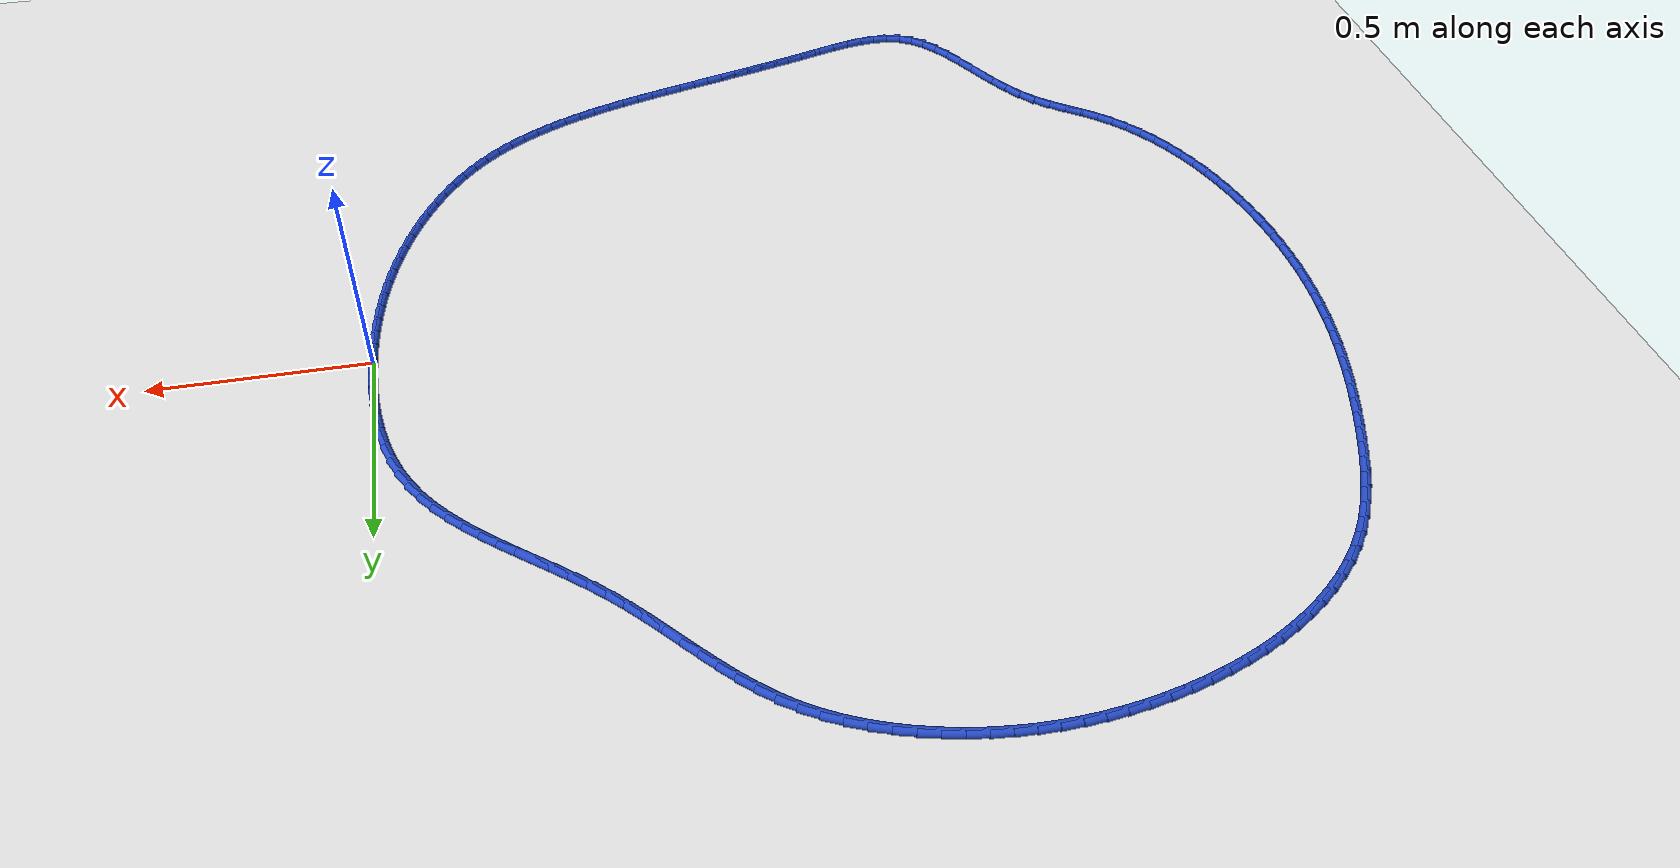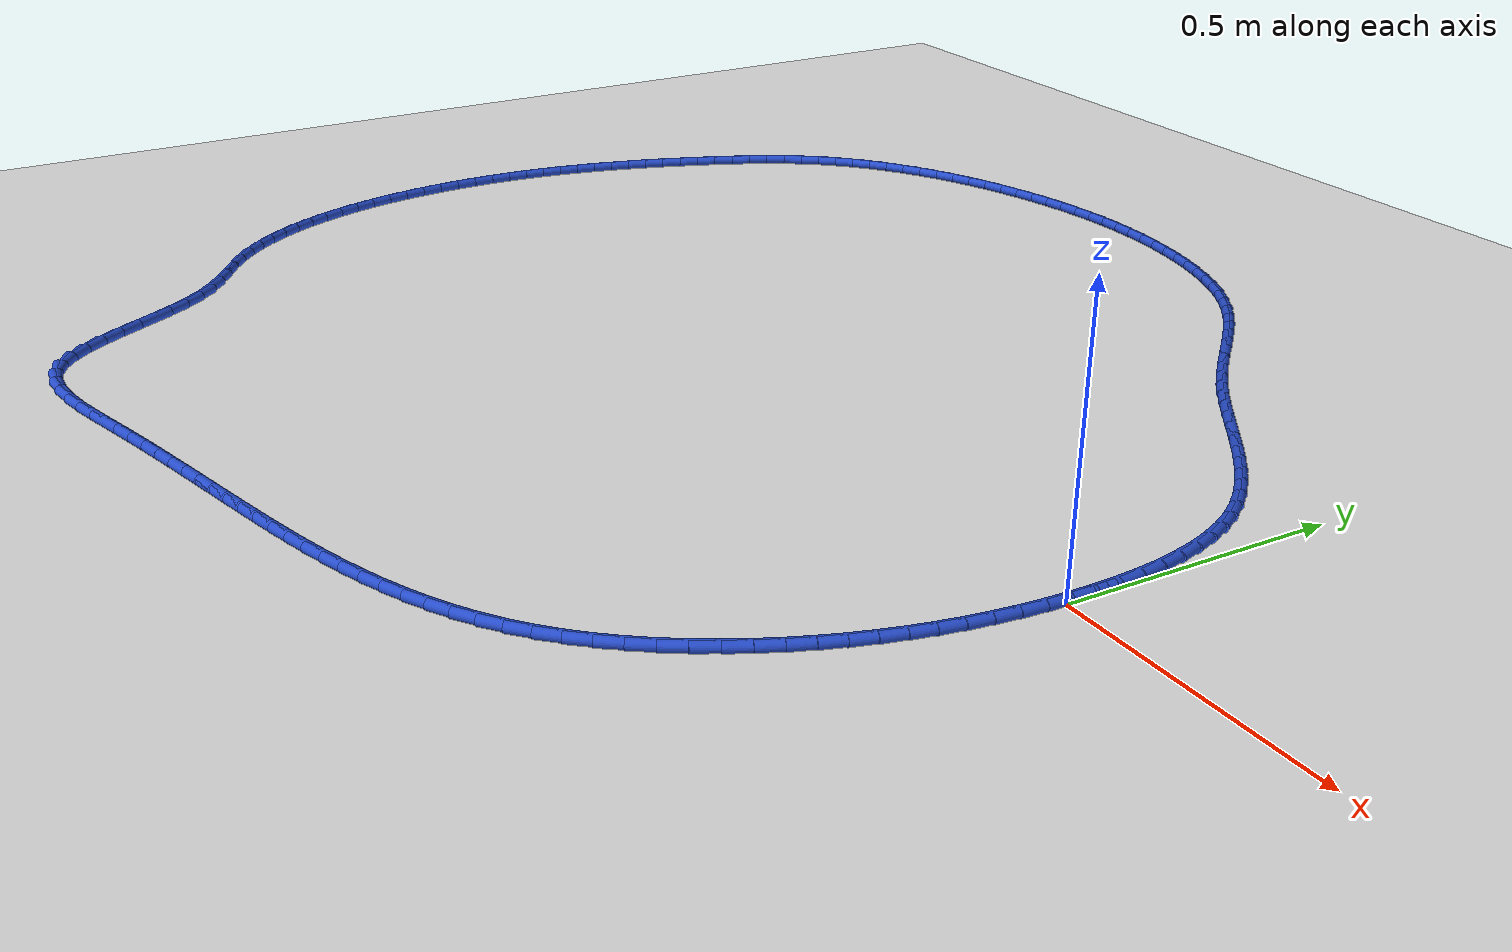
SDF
<sdf version="1.6">
 <world name="default">
  <light name="sun" type="directional">
   <pose>0 0 10 0 -0 0</pose>
   <diffuse>0.8 0.8 0.8 1</diffuse>
   <specular>0.2 0.2 0.2 1</specular>
   <attenuation>
    <range>1000</range>
    <constant>0.9</constant>
    <linear>0.01</linear>
    <quadratic>0.001</quadratic>
   </attenuation>
   <direction>-0.5 0.1 -0.9</direction>
  </light>
  <model name="ground_plane">
   <static>1</static>
   <link name="link">
    <collision name="collision">
     <geometry><plane><normal>0 0 1</normal><size>100 100</size></plane></geometry>
     <surface><friction><ode><mu>100</mu><mu2>50</mu2></ode></friction></surface>
    </collision>
    <visual name="visual">
     <cast_shadows>0</cast_shadows>
     <geometry><plane><normal>0 0 1</normal><size>100 100</size></plane></geometry>
     <material>
      <script><uri>file://media/materials/scripts/gazebo.material</uri><name>Gazebo/WhiteGlow</name></script>
     </material>
    </visual>
   </link>
  </model>
  <gravity>0 0 -9.8</gravity>
  <magnetic_field>6e-06 2.3e-05 -4.2e-05</magnetic_field>
  <atmosphere type="adiabatic"/>
  <physics name="default_physics" default="0" type="ode">
   <max_step_size>0.001</max_step_size>
   <real_time_factor>1</real_time_factor>
   <real_time_update_rate>1000</real_time_update_rate>
  </physics>
  <scene><ambient>0.4 0.4 0.4 1</ambient><background>0.7 0.7 0.7 1</background><shadows>1</shadows></scene>
  <spherical_coordinates>
   <surface_model>EARTH_WGS84</surface_model>
   <latitude_deg>0</latitude_deg>
   <longitude_deg>0</longitude_deg>
   <elevation>0</elevation>
   <heading_deg>0</heading_deg>
  </spherical_coordinates>
  <model name="line">
   <link name="link_0">
    <pose>1.3877787807814457e-17 8.326672684688674e-17 0.01 0 1.57 1.5598768106057224</pose>
    <collision name="collision">
     <geometry><cylinder><radius>0.01</radius><length>0.08</length></cylinder></geometry>
    </collision>
    <visual name="visual">
     <material>
      <script><name>Gazebo/Blue</name><uri>file://media/materials/scripts/gazebo.material</uri></script>
     </material>
     <geometry><cylinder><radius>0.01</radius><length>0.08</length></cylinder></geometry>
    </visual>
   </link>
   <link name="link_1">
    <pose>0.0004836907167628415 0.044294223645875125 0.01 0 1.57 -1.5435371216451328</pose>
    <collision name="collision">
     <geometry><cylinder><radius>0.01</radius><length>0.08</length></cylinder></geometry>
    </collision>
    <visual name="visual">
     <material>
      <script><name>Gazebo/Blue</name><uri>file://media/materials/scripts/gazebo.material</uri></script>
     </material>
     <geometry><cylinder><radius>0.01</radius><length>0.08</length></cylinder></geometry>
    </visual>
   </link>
   <link name="link_2">
    <pose>-0.0007289443741423879 0.08876854760715641 0.01 0 1.57 -1.5006337312821414</pose>
    <collision name="collision">
     <geometry><cylinder><radius>0.01</radius><length>0.08</length></cylinder></geometry>
    </collision>
    <visual name="visual">
     <material>
      <script><name>Gazebo/Blue</name><uri>file://media/materials/scripts/gazebo.material</uri></script>
     </material>
     <geometry><cylinder><radius>0.01</radius><length>0.08</length></cylinder></geometry>
    </visual>
   </link>
   <link name="link_3">
    <pose>-0.00384553250703105 0.133115144653902 0.01 0 1.57 -1.4522914731728134</pose>
    <collision name="collision">
     <geometry><cylinder><radius>0.01</radius><length>0.08</length></cylinder></geometry>
    </collision>
    <visual name="visual">
     <material>
      <script><name>Gazebo/Blue</name><uri>file://media/materials/scripts/gazebo.material</uri></script>
     </material>
     <geometry><cylinder><radius>0.01</radius><length>0.08</length></cylinder></geometry>
    </visual>
   </link>
   <link name="link_4">
    <pose>-0.00907370091621851 0.1770261875561697 0.01 0 1.57 -1.3977072143953841</pose>
    <collision name="collision">
     <geometry><cylinder><radius>0.01</radius><length>0.08</length></cylinder></geometry>
    </collision>
    <visual name="visual">
     <material>
      <script><name>Gazebo/Blue</name><uri>file://media/materials/scripts/gazebo.material</uri></script>
     </material>
     <geometry><cylinder><radius>0.01</radius><length>0.08</length></cylinder></geometry>
    </visual>
   </link>
   <link name="link_5">
    <pose>-0.016621076836020144 0.22019384908401765 0.01 0 1.57 -1.3360089207550203</pose>
    <collision name="collision">
     <geometry><cylinder><radius>0.01</radius><length>0.08</length></cylinder></geometry>
    </collision>
    <visual name="visual">
     <material>
      <script><name>Gazebo/Blue</name><uri>file://media/materials/scripts/gazebo.material</uri></script>
     </material>
     <geometry><cylinder><radius>0.01</radius><length>0.08</length></cylinder></geometry>
    </visual>
   </link>
   <link name="link_6">
    <pose>-0.026695287500751324 0.2623103020075036 0.01 0 1.57 -1.2663033365061571</pose>
    <collision name="collision">
     <geometry><cylinder><radius>0.01</radius><length>0.08</length></cylinder></geometry>
    </collision>
    <visual name="visual">
     <material>
      <script><name>Gazebo/Blue</name><uri>file://media/materials/scripts/gazebo.material</uri></script>
     </material>
     <geometry><cylinder><radius>0.01</radius><length>0.08</length></cylinder></geometry>
    </visual>
   </link>
   <link name="link_7">
    <pose>-0.039503960144727415 0.30306771909668556 0.01 0 1.57 -1.1877665340091048</pose>
    <collision name="collision">
     <geometry><cylinder><radius>0.01</radius><length>0.08</length></cylinder></geometry>
    </collision>
    <visual name="visual">
     <material>
      <script><name>Gazebo/Blue</name><uri>file://media/materials/scripts/gazebo.material</uri></script>
     </material>
     <geometry><cylinder><radius>0.01</radius><length>0.08</length></cylinder></geometry>
    </visual>
   </link>
   <link name="link_8">
    <pose>-0.05525472200226378 0.34215827312162156 0.01 0 1.57 -1.099792717606727</pose>
    <collision name="collision">
     <geometry><cylinder><radius>0.01</radius><length>0.08</length></cylinder></geometry>
    </collision>
    <visual name="visual">
     <material>
      <script><name>Gazebo/Blue</name><uri>file://media/materials/scripts/gazebo.material</uri></script>
     </material>
     <geometry><cylinder><radius>0.01</radius><length>0.08</length></cylinder></geometry>
    </visual>
   </link>
   <link name="link_9">
    <pose>-0.07415520030767579 0.37927413685236944 0.01 0 1.57 -1.0047245370595015</pose>
    <collision name="collision">
     <geometry><cylinder><radius>0.01</radius><length>0.08</length></cylinder></geometry>
    </collision>
    <visual name="visual">
     <material>
      <script><name>Gazebo/Blue</name><uri>file://media/materials/scripts/gazebo.material</uri></script>
     </material>
     <geometry><cylinder><radius>0.01</radius><length>0.08</length></cylinder></geometry>
    </visual>
   </link>
   <link name="link_10">
    <pose>-0.0963375335057452 0.4141827364127885 0.01 0 1.57 -0.9168224138754677</pose>
    <collision name="collision">
     <geometry><cylinder><radius>0.01</radius><length>0.08</length></cylinder></geometry>
    </collision>
    <visual name="visual">
     <material>
      <script><name>Gazebo/Blue</name><uri>file://media/materials/scripts/gazebo.material</uri></script>
     </material>
     <geometry><cylinder><radius>0.01</radius><length>0.08</length></cylinder></geometry>
    </visual>
   </link>
   <link name="link_11">
    <pose>-0.1215318323017977 0.4470522718151822 0.01 0 1.57 -0.8418158129822889</pose>
    <collision name="collision">
     <geometry><cylinder><radius>0.01</radius><length>0.08</length></cylinder></geometry>
    </collision>
    <visual name="visual">
     <material>
      <script><name>Gazebo/Blue</name><uri>file://media/materials/scripts/gazebo.material</uri></script>
     </material>
     <geometry><cylinder><radius>0.01</radius><length>0.08</length></cylinder></geometry>
    </visual>
   </link>
   <link name="link_12">
    <pose>-0.14933490482825906 0.47818382989840136 0.01 0 1.57 -0.7801420067670627</pose>
    <collision name="collision">
     <geometry><cylinder><radius>0.01</radius><length>0.08</length></cylinder></geometry>
    </collision>
    <visual name="visual">
     <material>
      <script><name>Gazebo/Blue</name><uri>file://media/materials/scripts/gazebo.material</uri></script>
     </material>
     <geometry><cylinder><radius>0.01</radius><length>0.08</length></cylinder></geometry>
    </visual>
   </link>
   <link name="link_13">
    <pose>-0.17934347213868584 0.5078785843085829 0.01 0 1.57 -0.7315879150065248</pose>
    <collision name="collision">
     <geometry><cylinder><radius>0.01</radius><length>0.08</length></cylinder></geometry>
    </collision>
    <visual name="visual">
     <material>
      <script><name>Gazebo/Blue</name><uri>file://media/materials/scripts/gazebo.material</uri></script>
     </material>
     <geometry><cylinder><radius>0.01</radius><length>0.08</length></cylinder></geometry>
    </visual>
   </link>
   <link name="link_14">
    <pose>-0.21115425528663528 0.5364377086918644 0.01 0 1.57 -0.6956244081678113</pose>
    <collision name="collision">
     <geometry><cylinder><radius>0.01</radius><length>0.08</length></cylinder></geometry>
    </collision>
    <visual name="visual">
     <material>
      <script><name>Gazebo/Blue</name><uri>file://media/materials/scripts/gazebo.material</uri></script>
     </material>
     <geometry><cylinder><radius>0.01</radius><length>0.08</length></cylinder></geometry>
    </visual>
   </link>
   <link name="link_15">
    <pose>-0.24436397532566392 0.5641623766943822 0.01 0 1.57 -0.6716508556180303</pose>
    <collision name="collision">
     <geometry><cylinder><radius>0.01</radius><length>0.08</length></cylinder></geometry>
    </collision>
    <visual name="visual">
     <material>
      <script><name>Gazebo/Blue</name><uri>file://media/materials/scripts/gazebo.material</uri></script>
     </material>
     <geometry><cylinder><radius>0.01</radius><length>0.08</length></cylinder></geometry>
    </visual>
   </link>
   <link name="link_16">
    <pose>-0.27856935330932875 0.5913537619622738 0.01 0 1.57 -0.6591487235943367</pose>
    <collision name="collision">
     <geometry><cylinder><radius>0.01</radius><length>0.08</length></cylinder></geometry>
    </collision>
    <visual name="visual">
     <material>
      <script><name>Gazebo/Blue</name><uri>file://media/materials/scripts/gazebo.material</uri></script>
     </material>
     <geometry><cylinder><radius>0.01</radius><length>0.08</length></cylinder></geometry>
    </visual>
   </link>
   <link name="link_17">
    <pose>-0.31336711029118663 0.6183130381416758 0.01 0 1.57 -0.6577640735591304</pose>
    <collision name="collision">
     <geometry><cylinder><radius>0.01</radius><length>0.08</length></cylinder></geometry>
    </collision>
    <visual name="visual">
     <material>
      <script><name>Gazebo/Blue</name><uri>file://media/materials/scripts/gazebo.material</uri></script>
     </material>
     <geometry><cylinder><radius>0.01</radius><length>0.08</length></cylinder></geometry>
    </visual>
   </link>
   <link name="link_18">
    <pose>-0.3483539673247943 0.6453413788787257 0.01 0 1.57 -0.6673402630239551</pose>
    <collision name="collision">
     <geometry><cylinder><radius>0.01</radius><length>0.08</length></cylinder></geometry>
    </collision>
    <visual name="visual">
     <material>
      <script><name>Gazebo/Blue</name><uri>file://media/materials/scripts/gazebo.material</uri></script>
     </material>
     <geometry><cylinder><radius>0.01</radius><length>0.08</length></cylinder></geometry>
    </visual>
   </link>
   <link name="link_19">
    <pose>-0.38312664546370867 0.6727399578195599 0.01 0 1.57 -0.687914505725469</pose>
    <collision name="collision">
     <geometry><cylinder><radius>0.01</radius><length>0.08</length></cylinder></geometry>
    </collision>
    <visual name="visual">
     <material>
      <script><name>Gazebo/Blue</name><uri>file://media/materials/scripts/gazebo.material</uri></script>
     </material>
     <geometry><cylinder><radius>0.01</radius><length>0.08</length></cylinder></geometry>
    </visual>
   </link>
   <link name="link_20">
    <pose>-0.4172818657614865 0.700809948610316 0.01 0 1.57 -0.7196823648466406</pose>
    <collision name="collision">
     <geometry><cylinder><radius>0.01</radius><length>0.08</length></cylinder></geometry>
    </collision>
    <visual name="visual">
     <material>
      <script><name>Gazebo/Blue</name><uri>file://media/materials/scripts/gazebo.material</uri></script>
     </material>
     <geometry><cylinder><radius>0.01</radius><length>0.08</length></cylinder></geometry>
    </visual>
   </link>
   <link name="link_21">
    <pose>-0.45041634927168483 0.7298525248971306 0.01 0 1.57 -0.7610096852235865</pose>
    <collision name="collision">
     <geometry><cylinder><radius>0.01</radius><length>0.08</length></cylinder></geometry>
    </collision>
    <visual name="visual">
     <material>
      <script><name>Gazebo/Blue</name><uri>file://media/materials/scripts/gazebo.material</uri></script>
     </material>
     <geometry><cylinder><radius>0.01</radius><length>0.08</length></cylinder></geometry>
    </visual>
   </link>
   <link name="link_22">
    <pose>-0.4821890321233908 0.7601120368964726 0.01 0 1.57 -0.797152304627542</pose>
    <collision name="collision">
     <geometry><cylinder><radius>0.01</radius><length>0.08</length></cylinder></geometry>
    </collision>
    <visual name="visual">
     <material>
      <script><name>Gazebo/Blue</name><uri>file://media/materials/scripts/gazebo.material</uri></script>
     </material>
     <geometry><cylinder><radius>0.01</radius><length>0.08</length></cylinder></geometry>
    </visual>
   </link>
   <link name="link_23">
    <pose>-0.512741858784416 0.7913916846673803 0.01 0 1.57 -0.8210310841916981</pose>
    <collision name="collision">
     <geometry><cylinder><radius>0.01</radius><length>0.08</length></cylinder></geometry>
    </collision>
    <visual name="visual">
     <material>
      <script><name>Gazebo/Blue</name><uri>file://media/materials/scripts/gazebo.material</uri></script>
     </material>
     <geometry><cylinder><radius>0.01</radius><length>0.08</length></cylinder></geometry>
    </visual>
   </link>
   <link name="link_24">
    <pose>-0.5424426831592627 0.8232883364614045 0.01 0 1.57 -0.8325101597866503</pose>
    <collision name="collision">
     <geometry><cylinder><radius>0.01</radius><length>0.08</length></cylinder></geometry>
    </collision>
    <visual name="visual">
     <material>
      <script><name>Gazebo/Blue</name><uri>file://media/materials/scripts/gazebo.material</uri></script>
     </material>
     <geometry><cylinder><radius>0.01</radius><length>0.08</length></cylinder></geometry>
    </visual>
   </link>
   <link name="link_25">
    <pose>-0.5716606430352817 0.8553976879103389 0.01 0 1.57 -0.8314720935630214</pose>
    <collision name="collision">
     <geometry><cylinder><radius>0.01</radius><length>0.08</length></cylinder></geometry>
    </collision>
    <visual name="visual">
     <material>
      <script><name>Gazebo/Blue</name><uri>file://media/materials/scripts/gazebo.material</uri></script>
     </material>
     <geometry><cylinder><radius>0.01</radius><length>0.08</length></cylinder></geometry>
    </visual>
   </link>
   <link name="link_26">
    <pose>-0.600764876199824 0.887315434645976 0.01 0 1.57 -0.8177228509698592</pose>
    <collision name="collision">
     <geometry><cylinder><radius>0.01</radius><length>0.08</length></cylinder></geometry>
    </collision>
    <visual name="visual">
     <material>
      <script><name>Gazebo/Blue</name><uri>file://media/materials/scripts/gazebo.material</uri></script>
     </material>
     <geometry><cylinder><radius>0.01</radius><length>0.08</length></cylinder></geometry>
    </visual>
   </link>
   <link name="link_27">
    <pose>-0.6301245204402404 0.9186372723001099 0.01 0 1.57 -0.7909934375270149</pose>
    <collision name="collision">
     <geometry><cylinder><radius>0.01</radius><length>0.08</length></cylinder></geometry>
    </collision>
    <visual name="visual">
     <material>
      <script><name>Gazebo/Blue</name><uri>file://media/materials/scripts/gazebo.material</uri></script>
     </material>
     <geometry><cylinder><radius>0.01</radius><length>0.08</length></cylinder></geometry>
    </visual>
   </link>
   <link name="link_28">
    <pose>-0.6601087135438817 0.9489588965045337 0.01 0 1.57 -0.7510052885653716</pose>
    <collision name="collision">
     <geometry><cylinder><radius>0.01</radius><length>0.08</length></cylinder></geometry>
    </collision>
    <visual name="visual">
     <material>
      <script><name>Gazebo/Blue</name><uri>file://media/materials/scripts/gazebo.material</uri></script>
     </material>
     <geometry><cylinder><radius>0.01</radius><length>0.08</length></cylinder></geometry>
    </visual>
   </link>
   <link name="link_29">
    <pose>-0.691086593298099 0.9778760028910407 0.01 0 1.57 -0.6976090979489733</pose>
    <collision name="collision">
     <geometry><cylinder><radius>0.01</radius><length>0.08</length></cylinder></geometry>
    </collision>
    <visual name="visual">
     <material>
      <script><name>Gazebo/Blue</name><uri>file://media/materials/scripts/gazebo.material</uri></script>
     </material>
     <geometry><cylinder><radius>0.01</radius><length>0.08</length></cylinder></geometry>
    </visual>
   </link>
   <link name="link_30">
    <pose>-0.7234272974902427 1.004984287091424 0.01 0 1.57 -0.6310009686447844</pose>
    <collision name="collision">
     <geometry><cylinder><radius>0.01</radius><length>0.08</length></cylinder></geometry>
    </collision>
    <visual name="visual">
     <material>
      <script><name>Gazebo/Blue</name><uri>file://media/materials/scripts/gazebo.material</uri></script>
     </material>
     <geometry><cylinder><radius>0.01</radius><length>0.08</length></cylinder></geometry>
    </visual>
   </link>
   <link name="link_31">
    <pose>-0.7574999639076643 1.0298794447374777 0.01 0 1.57 -0.5545024217298062</pose>
    <collision name="collision">
     <geometry><cylinder><radius>0.01</radius><length>0.08</length></cylinder></geometry>
    </collision>
    <visual name="visual">
     <material>
      <script><name>Gazebo/Blue</name><uri>file://media/materials/scripts/gazebo.material</uri></script>
     </material>
     <geometry><cylinder><radius>0.01</radius><length>0.08</length></cylinder></geometry>
    </visual>
   </link>
   <link name="link_32">
    <pose>-0.7935826733913394 1.0522260901025822 0.01 0 1.57 -0.48122745938894457</pose>
    <collision name="collision">
     <geometry><cylinder><radius>0.01</radius><length>0.08</length></cylinder></geometry>
    </collision>
    <visual name="visual">
     <material>
      <script><name>Gazebo/Blue</name><uri>file://media/materials/scripts/gazebo.material</uri></script>
     </material>
     <geometry><cylinder><radius>0.01</radius><length>0.08</length></cylinder></geometry>
    </visual>
   </link>
   <link name="link_33">
    <pose>-0.8315051828435908 1.072028162224167 0.01 0 1.57 -0.41462984590011337</pose>
    <collision name="collision">
     <geometry><cylinder><radius>0.01</radius><length>0.08</length></cylinder></geometry>
    </collision>
    <visual name="visual">
     <material>
      <script><name>Gazebo/Blue</name><uri>file://media/materials/scripts/gazebo.material</uri></script>
     </material>
     <geometry><cylinder><radius>0.01</radius><length>0.08</length></cylinder></geometry>
    </visual>
   </link>
   <link name="link_34">
    <pose>-0.8709595048268142 1.0893938552588143 0.01 0 1.57 -0.35409090840076</pose>
    <collision name="collision">
     <geometry><cylinder><radius>0.01</radius><length>0.08</length></cylinder></geometry>
    </collision>
    <visual name="visual">
     <material>
      <script><name>Gazebo/Blue</name><uri>file://media/materials/scripts/gazebo.material</uri></script>
     </material>
     <geometry><cylinder><radius>0.01</radius><length>0.08</length></cylinder></geometry>
    </visual>
   </link>
   <link name="link_35">
    <pose>-0.9116376147383644 1.1044313914923638 0.01 0 1.57 -0.29892685950490777</pose>
    <collision name="collision">
     <geometry><cylinder><radius>0.01</radius><length>0.08</length></cylinder></geometry>
    </collision>
    <visual name="visual">
     <material>
      <script><name>Gazebo/Blue</name><uri>file://media/materials/scripts/gazebo.material</uri></script>
     </material>
     <geometry><cylinder><radius>0.01</radius><length>0.08</length></cylinder></geometry>
    </visual>
   </link>
   <link name="link_36">
    <pose>-0.9532314879755962 1.1172489932106544 0.01 0 1.57 -0.24844329132971615</pose>
    <collision name="collision">
     <geometry><cylinder><radius>0.01</radius><length>0.08</length></cylinder></geometry>
    </collision>
    <visual name="visual">
     <material>
      <script><name>Gazebo/Blue</name><uri>file://media/materials/scripts/gazebo.material</uri></script>
     </material>
     <geometry><cylinder><radius>0.01</radius><length>0.08</length></cylinder></geometry>
    </visual>
   </link>
   <link name="link_37">
    <pose>-0.9954330999358645 1.1279548826995254 0.01 0 1.57 -0.2019263581818744</pose>
    <collision name="collision">
     <geometry><cylinder><radius>0.01</radius><length>0.08</length></cylinder></geometry>
    </collision>
    <visual name="visual">
     <material>
      <script><name>Gazebo/Blue</name><uri>file://media/materials/scripts/gazebo.material</uri></script>
     </material>
     <geometry><cylinder><radius>0.01</radius><length>0.08</length></cylinder></geometry>
    </visual>
   </link>
   <link name="link_38">
    <pose>-1.0379380443879933 1.1366563392020417 0.01 0 1.57 -0.15752989335012374</pose>
    <collision name="collision">
     <geometry><cylinder><radius>0.01</radius><length>0.08</length></cylinder></geometry>
    </collision>
    <visual name="visual">
     <material>
      <script><name>Gazebo/Blue</name><uri>file://media/materials/scripts/gazebo.material</uri></script>
     </material>
     <geometry><cylinder><radius>0.01</radius><length>0.08</length></cylinder></geometry>
    </visual>
   </link>
   <link name="link_39">
    <pose>-1.0805676246525286 1.1434278787457348 0.01 0 1.57 -0.11361183679511512</pose>
    <collision name="collision">
     <geometry><cylinder><radius>0.01</radius><length>0.08</length></cylinder></geometry>
    </collision>
    <visual name="visual">
     <material>
      <script><name>Gazebo/Blue</name><uri>file://media/materials/scripts/gazebo.material</uri></script>
     </material>
     <geometry><cylinder><radius>0.01</radius><length>0.08</length></cylinder></geometry>
    </visual>
   </link>
   <link name="link_40">
    <pose>-1.1232982848768864 1.1483035835782072 0.01 0 1.57 -0.07021624613493332</pose>
    <collision name="collision">
     <geometry><cylinder><radius>0.01</radius><length>0.08</length></cylinder></geometry>
    </collision>
    <visual name="visual">
     <material>
      <script><name>Gazebo/Blue</name><uri>file://media/materials/scripts/gazebo.material</uri></script>
     </material>
     <geometry><cylinder><radius>0.01</radius><length>0.08</length></cylinder></geometry>
    </visual>
   </link>
   <link name="link_41">
    <pose>-1.1661160556076502 1.151315037479302 0.01 0 1.57 -0.027476452278554456</pose>
    <collision name="collision">
     <geometry><cylinder><radius>0.01</radius><length>0.08</length></cylinder></geometry>
    </collision>
    <visual name="visual">
     <material>
      <script><name>Gazebo/Blue</name><uri>file://media/materials/scripts/gazebo.material</uri></script>
     </material>
     <geometry><cylinder><radius>0.01</radius><length>0.08</length></cylinder></geometry>
    </visual>
   </link>
   <link name="link_42">
    <pose>-1.2090069673914028 1.1524938242288623 0.01 0 1.57 0.014487820118626262</pose>
    <collision name="collision">
     <geometry><cylinder><radius>0.01</radius><length>0.08</length></cylinder></geometry>
    </collision>
    <visual name="visual">
     <material>
      <script><name>Gazebo/Blue</name><uri>file://media/materials/scripts/gazebo.material</uri></script>
     </material>
     <geometry><cylinder><radius>0.01</radius><length>0.08</length></cylinder></geometry>
    </visual>
   </link>
   <link name="link_43">
    <pose>-1.2519570507747277 1.1518715276067315 0.01 0 1.57 0.05557198948166423</pose>
    <collision name="collision">
     <geometry><cylinder><radius>0.01</radius><length>0.08</length></cylinder></geometry>
    </collision>
    <visual name="visual">
     <material>
      <script><name>Gazebo/Blue</name><uri>file://media/materials/scripts/gazebo.material</uri></script>
     </material>
     <geometry><cylinder><radius>0.01</radius><length>0.08</length></cylinder></geometry>
    </visual>
   </link>
   <link name="link_44">
    <pose>-1.2949523363042093 1.1494797313927527 0.01 0 1.57 0.0956875080335254</pose>
    <collision name="collision">
     <geometry><cylinder><radius>0.01</radius><length>0.08</length></cylinder></geometry>
    </collision>
    <visual name="visual">
     <material>
      <script><name>Gazebo/Blue</name><uri>file://media/materials/scripts/gazebo.material</uri></script>
     </material>
     <geometry><cylinder><radius>0.01</radius><length>0.08</length></cylinder></geometry>
    </visual>
   </link>
   <link name="link_45">
    <pose>-1.3379788545264293 1.1453500193667683 0.01 0 1.57 0.13476213916483035</pose>
    <collision name="collision">
     <geometry><cylinder><radius>0.01</radius><length>0.08</length></cylinder></geometry>
    </collision>
    <visual name="visual">
     <material>
      <script><name>Gazebo/Blue</name><uri>file://media/materials/scripts/gazebo.material</uri></script>
     </material>
     <geometry><cylinder><radius>0.01</radius><length>0.08</length></cylinder></geometry>
    </visual>
   </link>
   <link name="link_46">
    <pose>-1.381022635987973 1.1395139753086223 0.01 0 1.57 0.17273969000459943</pose>
    <collision name="collision">
     <geometry><cylinder><radius>0.01</radius><length>0.08</length></cylinder></geometry>
    </collision>
    <visual name="visual">
     <material>
      <script><name>Gazebo/Blue</name><uri>file://media/materials/scripts/gazebo.material</uri></script>
     </material>
     <geometry><cylinder><radius>0.01</radius><length>0.08</length></cylinder></geometry>
    </visual>
   </link>
   <link name="link_47">
    <pose>-1.4240697112354217 1.132003182998157 0.01 0 1.57 0.2096071957228121</pose>
    <collision name="collision">
     <geometry><cylinder><radius>0.01</radius><length>0.08</length></cylinder></geometry>
    </collision>
    <visual name="visual">
     <material>
      <script><name>Gazebo/Blue</name><uri>file://media/materials/scripts/gazebo.material</uri></script>
     </material>
     <geometry><cylinder><radius>0.01</radius><length>0.08</length></cylinder></geometry>
    </visual>
   </link>
   <link name="link_48">
    <pose>-1.4671038384614792 1.1228484543832284 0.01 0 1.57 0.24628461708831745</pose>
    <collision name="collision">
     <geometry><cylinder><radius>0.01</radius><length>0.08</length></cylinder></geometry>
    </collision>
    <visual name="visual">
     <material>
      <script><name>Gazebo/Blue</name><uri>file://media/materials/scripts/gazebo.material</uri></script>
     </material>
     <geometry><cylinder><radius>0.01</radius><length>0.08</length></cylinder></geometry>
    </visual>
   </link>
   <link name="link_49">
    <pose>-1.5100358995711347 1.1120558481149296 0.01 0 1.57 0.2840749618697426</pose>
    <collision name="collision">
     <geometry><cylinder><radius>0.01</radius><length>0.08</length></cylinder></geometry>
    </collision>
    <visual name="visual">
     <material>
      <script><name>Gazebo/Blue</name><uri>file://media/materials/scripts/gazebo.material</uri></script>
     </material>
     <geometry><cylinder><radius>0.01</radius><length>0.08</length></cylinder></geometry>
    </visual>
   </link>
   <link name="link_50">
    <pose>-1.552690191509292 1.0996020132341846 0.01 0 1.57 0.3233465358810321</pose>
    <collision name="collision">
     <geometry><cylinder><radius>0.01</radius><length>0.08</length></cylinder></geometry>
    </collision>
    <visual name="visual">
     <material>
      <script><name>Gazebo/Blue</name><uri>file://media/materials/scripts/gazebo.material</uri></script>
     </material>
     <geometry><cylinder><radius>0.01</radius><length>0.08</length></cylinder></geometry>
    </visual>
   </link>
   <link name="link_51">
    <pose>-1.5948859715732062 1.0854618870057307 0.01 0 1.57 0.36440805415830435</pose>
    <collision name="collision">
     <geometry><cylinder><radius>0.01</radius><length>0.08</length></cylinder></geometry>
    </collision>
    <visual name="visual">
     <material>
      <script><name>Gazebo/Blue</name><uri>file://media/materials/scripts/gazebo.material</uri></script>
     </material>
     <geometry><cylinder><radius>0.01</radius><length>0.08</length></cylinder></geometry>
    </visual>
   </link>
   <link name="link_52">
    <pose>-1.636442497060127 1.0696104066943042 0.01 0 1.57 0.40757199093539087</pose>
    <collision name="collision">
     <geometry><cylinder><radius>0.01</radius><length>0.08</length></cylinder></geometry>
    </collision>
    <visual name="visual">
     <material>
      <script><name>Gazebo/Blue</name><uri>file://media/materials/scripts/gazebo.material</uri></script>
     </material>
     <geometry><cylinder><radius>0.01</radius><length>0.08</length></cylinder></geometry>
    </visual>
   </link>
   <link name="link_53">
    <pose>-1.6771790252673098 1.0520225095646425 0.01 0 1.57 0.45315391550806555</pose>
    <collision name="collision">
     <geometry><cylinder><radius>0.01</radius><length>0.08</length></cylinder></geometry>
    </collision>
    <visual name="visual">
     <material>
      <script><name>Gazebo/Blue</name><uri>file://media/materials/scripts/gazebo.material</uri></script>
     </material>
     <geometry><cylinder><radius>0.01</radius><length>0.08</length></cylinder></geometry>
    </visual>
   </link>
   <link name="link_54">
    <pose>-1.7169148134920063 1.0326731328814829 0.01 0 1.57 0.5014691511098146</pose>
    <collision name="collision">
     <geometry><cylinder><radius>0.01</radius><length>0.08</length></cylinder></geometry>
    </collision>
    <visual name="visual">
     <material>
      <script><name>Gazebo/Blue</name><uri>file://media/materials/scripts/gazebo.material</uri></script>
     </material>
     <geometry><cylinder><radius>0.01</radius><length>0.08</length></cylinder></geometry>
    </visual>
   </link>
   <link name="link_55">
    <pose>-1.75546911903147 1.0115372139095624 0.01 0 1.57 0.5528260169134608</pose>
    <collision name="collision">
     <geometry><cylinder><radius>0.01</radius><length>0.08</length></cylinder></geometry>
    </collision>
    <visual name="visual">
     <material>
      <script><name>Gazebo/Blue</name><uri>file://media/materials/scripts/gazebo.material</uri></script>
     </material>
     <geometry><cylinder><radius>0.01</radius><length>0.08</length></cylinder></geometry>
    </visual>
   </link>
   <link name="link_56">
    <pose>-1.7926611991829537 0.9885896899136176 0.01 0 1.57 0.6075147874828148</pose>
    <collision name="collision">
     <geometry><cylinder><radius>0.01</radius><length>0.08</length></cylinder></geometry>
    </collision>
    <visual name="visual">
     <material>
      <script><name>Gazebo/Blue</name><uri>file://media/materials/scripts/gazebo.material</uri></script>
     </material>
     <geometry><cylinder><radius>0.01</radius><length>0.08</length></cylinder></geometry>
    </visual>
   </link>
   <link name="link_57">
    <pose>-1.82831031124371 0.9638054981583861 0.01 0 1.57 0.6657915138858808</pose>
    <collision name="collision">
     <geometry><cylinder><radius>0.01</radius><length>0.08</length></cylinder></geometry>
    </collision>
    <visual name="visual">
     <material>
      <script><name>Gazebo/Blue</name><uri>file://media/materials/scripts/gazebo.material</uri></script>
     </material>
     <geometry><cylinder><radius>0.01</radius><length>0.08</length></cylinder></geometry>
    </visual>
   </link>
   <link name="link_58">
    <pose>-1.862235712510992 0.9371595759086044 0.01 0 1.57 0.7278561203931961</pose>
    <collision name="collision">
     <geometry><cylinder><radius>0.01</radius><length>0.08</length></cylinder></geometry>
    </collision>
    <visual name="visual">
     <material>
      <script><name>Gazebo/Blue</name><uri>file://media/materials/scripts/gazebo.material</uri></script>
     </material>
     <geometry><cylinder><radius>0.01</radius><length>0.08</length></cylinder></geometry>
    </visual>
   </link>
   <link name="link_59">
    <pose>-1.894256660282053 0.9086268604290104 0.01 0 1.57 0.7938248793110207</pose>
    <collision name="collision">
     <geometry><cylinder><radius>0.01</radius><length>0.08</length></cylinder></geometry>
    </collision>
    <visual name="visual">
     <material>
      <script><name>Gazebo/Blue</name><uri>file://media/materials/scripts/gazebo.material</uri></script>
     </material>
     <geometry><cylinder><radius>0.01</radius><length>0.08</length></cylinder></geometry>
    </visual>
   </link>
   <link name="link_60">
    <pose>-1.9241924118541454 0.8781822889843405 0.01 0 1.57 0.8636986211424419</pose>
    <collision name="collision">
     <geometry><cylinder><radius>0.01</radius><length>0.08</length></cylinder></geometry>
    </collision>
    <visual name="visual">
     <material>
      <script><name>Gazebo/Blue</name><uri>file://media/materials/scripts/gazebo.material</uri></script>
     </material>
     <geometry><cylinder><radius>0.01</radius><length>0.08</length></cylinder></geometry>
    </visual>
   </link>
   <link name="link_61">
    <pose>-1.9518622245245227 0.8458007988393315 0.01 0 1.57 0.9357653783498592</pose>
    <collision name="collision">
     <geometry><cylinder><radius>0.01</radius><length>0.08</length></cylinder></geometry>
    </collision>
    <visual name="visual">
     <material>
      <script><name>Gazebo/Blue</name><uri>file://media/materials/scripts/gazebo.material</uri></script>
     </material>
     <geometry><cylinder><radius>0.01</radius><length>0.08</length></cylinder></geometry>
    </visual>
   </link>
   <link name="link_62">
    <pose>-1.9771398031395968 0.8114958162180252 0.01 0 1.57 1.00153983812924</pose>
    <collision name="collision">
     <geometry><cylinder><radius>0.01</radius><length>0.08</length></cylinder></geometry>
    </collision>
    <visual name="visual">
     <material>
      <script><name>Gazebo/Blue</name><uri>file://media/materials/scripts/gazebo.material</uri></script>
     </material>
     <geometry><cylinder><radius>0.01</radius><length>0.08</length></cylinder></geometry>
    </visual>
   </link>
   <link name="link_63">
    <pose>-2.0001850677938275 0.7754830928339339 0.01 0 1.57 1.058255667308963</pose>
    <collision name="collision">
     <geometry><cylinder><radius>0.01</radius><length>0.08</length></cylinder></geometry>
    </collision>
    <visual name="visual">
     <material>
      <script><name>Gazebo/Blue</name><uri>file://media/materials/scripts/gazebo.material</uri></script>
     </material>
     <geometry><cylinder><radius>0.01</radius><length>0.08</length></cylinder></geometry>
    </visual>
   </link>
   <link name="link_64">
    <pose>-2.0212516559603655 0.7380446291928524 0.01 0 1.57 1.1061017269262252</pose>
    <collision name="collision">
     <geometry><cylinder><radius>0.01</radius><length>0.08</length></cylinder></geometry>
    </collision>
    <visual name="visual">
     <material>
      <script><name>Gazebo/Blue</name><uri>file://media/materials/scripts/gazebo.material</uri></script>
     </material>
     <geometry><cylinder><radius>0.01</radius><length>0.08</length></cylinder></geometry>
    </visual>
   </link>
   <link name="link_65">
    <pose>-2.040593259032498 0.699462463916707 0.01 0 1.57 1.1454029630622684</pose>
    <collision name="collision">
     <geometry><cylinder><radius>0.01</radius><length>0.08</length></cylinder></geometry>
    </collision>
    <visual name="visual">
     <material>
      <script><name>Gazebo/Blue</name><uri>file://media/materials/scripts/gazebo.material</uri></script>
     </material>
     <geometry><cylinder><radius>0.01</radius><length>0.08</length></cylinder></geometry>
    </visual>
   </link>
   <link name="link_66">
    <pose>-2.058463568403511 0.6600186356274222 0.01 0 1.57 1.1765105414277839</pose>
    <collision name="collision">
     <geometry><cylinder><radius>0.01</radius><length>0.08</length></cylinder></geometry>
    </collision>
    <visual name="visual">
     <material>
      <script><name>Gazebo/Blue</name><uri>file://media/materials/scripts/gazebo.material</uri></script>
     </material>
     <geometry><cylinder><radius>0.01</radius><length>0.08</length></cylinder></geometry>
    </visual>
   </link>
   <link name="link_67">
    <pose>-2.075116275466693 0.6199951829469256 0.01 0 1.57 1.1997668262292716</pose>
    <collision name="collision">
     <geometry><cylinder><radius>0.01</radius><length>0.08</length></cylinder></geometry>
    </collision>
    <visual name="visual">
     <material>
      <script><name>Gazebo/Blue</name><uri>file://media/materials/scripts/gazebo.material</uri></script>
     </material>
     <geometry><cylinder><radius>0.01</radius><length>0.08</length></cylinder></geometry>
    </visual>
   </link>
   <link name="link_68">
    <pose>-2.090803648119191 0.5796727235456463 0.01 0 1.57 1.218696845572907</pose>
    <collision name="collision">
     <geometry><cylinder><radius>0.01</radius><length>0.08</length></cylinder></geometry>
    </collision>
    <visual name="visual">
     <material>
      <script><name>Gazebo/Blue</name><uri>file://media/materials/scripts/gazebo.material</uri></script>
     </material>
     <geometry><cylinder><radius>0.01</radius><length>0.08</length></cylinder></geometry>
    </visual>
   </link>
   <link name="link_69">
    <pose>-2.1056662346330697 0.5392203551790877 0.01 0 1.57 1.2390229925777008</pose>
    <collision name="collision">
     <geometry><cylinder><radius>0.01</radius><length>0.08</length></cylinder></geometry>
    </collision>
    <visual name="visual">
     <material>
      <script><name>Gazebo/Blue</name><uri>file://media/materials/scripts/gazebo.material</uri></script>
     </material>
     <geometry><cylinder><radius>0.01</radius><length>0.08</length></cylinder></geometry>
    </visual>
   </link>
   <link name="link_70">
    <pose>-2.11965430994449 0.49861724239972244 0.01 0 1.57 1.2612830900050607</pose>
    <collision name="collision">
     <geometry><cylinder><radius>0.01</radius><length>0.08</length></cylinder></geometry>
    </collision>
    <visual name="visual">
     <material>
      <script><name>Gazebo/Blue</name><uri>file://media/materials/scripts/gazebo.material</uri></script>
     </material>
     <geometry><cylinder><radius>0.01</radius><length>0.08</length></cylinder></geometry>
    </visual>
   </link>
   <link name="link_71">
    <pose>-2.132699604497532 0.4578240384181035 0.01 0 1.57 1.285445899426974</pose>
    <collision name="collision">
     <geometry><cylinder><radius>0.01</radius><length>0.08</length></cylinder></geometry>
    </collision>
    <visual name="visual">
     <material>
      <script><name>Gazebo/Blue</name><uri>file://media/materials/scripts/gazebo.material</uri></script>
     </material>
     <geometry><cylinder><radius>0.01</radius><length>0.08</length></cylinder></geometry>
    </visual>
   </link>
   <link name="link_72">
    <pose>-2.1447338487362777 0.4168013964447853 0.01 0 1.57 1.311463314324935</pose>
    <collision name="collision">
     <geometry><cylinder><radius>0.01</radius><length>0.08</length></cylinder></geometry>
    </collision>
    <visual name="visual">
     <material>
      <script><name>Gazebo/Blue</name><uri>file://media/materials/scripts/gazebo.material</uri></script>
     </material>
     <geometry><cylinder><radius>0.01</radius><length>0.08</length></cylinder></geometry>
    </visual>
   </link>
   <link name="link_73">
    <pose>-2.1556887731048078 0.37550996969032063 0.01 0 1.57 1.3392682920328736</pose>
    <collision name="collision">
     <geometry><cylinder><radius>0.01</radius><length>0.08</length></cylinder></geometry>
    </collision>
    <visual name="visual">
     <material>
      <script><name>Gazebo/Blue</name><uri>file://media/materials/scripts/gazebo.material</uri></script>
     </material>
     <geometry><cylinder><radius>0.01</radius><length>0.08</length></cylinder></geometry>
    </visual>
   </link>
   <link name="link_74">
    <pose>-2.165496108047202 0.3339104113652638 0.01 0 1.57 1.3687731327968193</pose>
    <collision name="collision">
     <geometry><cylinder><radius>0.01</radius><length>0.08</length></cylinder></geometry>
    </collision>
    <visual name="visual">
     <material>
      <script><name>Gazebo/Blue</name><uri>file://media/materials/scripts/gazebo.material</uri></script>
     </material>
     <geometry><cylinder><radius>0.01</radius><length>0.08</length></cylinder></geometry>
    </visual>
   </link>
   <link name="link_75">
    <pose>-2.1740875840075433 0.2919633746801679 0.01 0 1.57 1.3998682957806359</pose>
    <collision name="collision">
     <geometry><cylinder><radius>0.01</radius><length>0.08</length></cylinder></geometry>
    </collision>
    <visual name="visual">
     <material>
      <script><name>Gazebo/Blue</name><uri>file://media/materials/scripts/gazebo.material</uri></script>
     </material>
     <geometry><cylinder><radius>0.01</radius><length>0.08</length></cylinder></geometry>
    </visual>
   </link>
   <link name="link_76">
    <pose>-2.1813949314299115 0.24962951284558613 0.01 0 1.57 1.432421943132091</pose>
    <collision name="collision">
     <geometry><cylinder><radius>0.01</radius><length>0.08</length></cylinder></geometry>
    </collision>
    <visual name="visual">
     <material>
      <script><name>Gazebo/Blue</name><uri>file://media/materials/scripts/gazebo.material</uri></script>
     </material>
     <geometry><cylinder><radius>0.01</radius><length>0.08</length></cylinder></geometry>
    </visual>
   </link>
   <link name="link_77">
    <pose>-2.1873498807583878 0.20686947907207287 0.01 0 1.57 1.4662803823805088</pose>
    <collision name="collision">
     <geometry><cylinder><radius>0.01</radius><length>0.08</length></cylinder></geometry>
    </collision>
    <visual name="visual">
     <material>
      <script><name>Gazebo/Blue</name><uri>file://media/materials/scripts/gazebo.material</uri></script>
     </material>
     <geometry><cylinder><radius>0.01</radius><length>0.08</length></cylinder></geometry>
    </visual>
   </link>
   <link name="link_78">
    <pose>-2.191884162437053 0.16364392657018073 0.01 0 1.57 1.501269530837358</pose>
    <collision name="collision">
     <geometry><cylinder><radius>0.01</radius><length>0.08</length></cylinder></geometry>
    </collision>
    <visual name="visual">
     <material>
      <script><name>Gazebo/Blue</name><uri>file://media/materials/scripts/gazebo.material</uri></script>
     </material>
     <geometry><cylinder><radius>0.01</radius><length>0.08</length></cylinder></geometry>
    </visual>
   </link>
   <link name="link_79">
    <pose>-2.194929506909988 0.11991350855046419 0.01 0 1.57 1.5371971469965724</pose>
    <collision name="collision">
     <geometry><cylinder><radius>0.01</radius><length>0.08</length></cylinder></geometry>
    </collision>
    <visual name="visual">
     <material>
      <script><name>Gazebo/Blue</name><uri>file://media/materials/scripts/gazebo.material</uri></script>
     </material>
     <geometry><cylinder><radius>0.01</radius><length>0.08</length></cylinder></geometry>
    </visual>
   </link>
   <link name="link_80">
    <pose>-2.1964176552986836 0.0756389648617756 0.01 0 1.57 -1.5678817399227625</pose>
    <collision name="collision">
     <geometry><cylinder><radius>0.01</radius><length>0.08</length></cylinder></geometry>
    </collision>
    <visual name="visual">
     <material>
      <script><name>Gazebo/Blue</name><uri>file://media/materials/scripts/gazebo.material</uri></script>
     </material>
     <geometry><cylinder><radius>0.01</radius><length>0.08</length></cylinder></geometry>
    </visual>
   </link>
   <link name="link_81">
    <pose>-2.1962870715884852 0.03083558580140903 0.01 0 1.57 -1.5311299063009747</pose>
    <collision name="collision">
     <geometry><cylinder><radius>0.01</radius><length>0.08</length></cylinder></geometry>
    </collision>
    <visual name="visual">
     <material>
      <script><name>Gazebo/Blue</name><uri>file://media/materials/scripts/gazebo.material</uri></script>
     </material>
     <geometry><cylinder><radius>0.01</radius><length>0.08</length></cylinder></geometry>
    </visual>
   </link>
   <link name="link_82">
    <pose>-2.1944944333536447 -0.014333550208515726 0.01 0 1.57 -1.493876951188243</pose>
    <collision name="collision">
     <geometry><cylinder><radius>0.01</radius><length>0.08</length></cylinder></geometry>
    </collision>
    <visual name="visual">
     <material>
      <script><name>Gazebo/Blue</name><uri>file://media/materials/scripts/gazebo.material</uri></script>
     </material>
     <geometry><cylinder><radius>0.01</radius><length>0.08</length></cylinder></geometry>
    </visual>
   </link>
   <link name="link_83">
    <pose>-2.1909994726579245 -0.05968058010404908 0.01 0 1.57 -1.4557814630714179</pose>
    <collision name="collision">
     <geometry><cylinder><radius>0.01</radius><length>0.08</length></cylinder></geometry>
    </collision>
    <visual name="visual">
     <material>
      <script><name>Gazebo/Blue</name><uri>file://media/materials/scripts/gazebo.material</uri></script>
     </material>
     <geometry><cylinder><radius>0.01</radius><length>0.08</length></cylinder></geometry>
    </visual>
   </link>
   <link name="link_84">
    <pose>-2.1857619215650894 -0.10501764082124379 0.01 0 1.57 -1.4165045528520377</pose>
    <collision name="collision">
     <geometry><cylinder><radius>0.01</radius><length>0.08</length></cylinder></geometry>
    </collision>
    <visual name="visual">
     <material>
      <script><name>Gazebo/Blue</name><uri>file://media/materials/scripts/gazebo.material</uri></script>
     </material>
     <geometry><cylinder><radius>0.01</radius><length>0.08</length></cylinder></geometry>
    </visual>
   </link>
   <link name="link_85">
    <pose>-2.1787415121389033 -0.15015686929615188 0.01 0 1.57 -1.3757044124202404</pose>
    <collision name="collision">
     <geometry><cylinder><radius>0.01</radius><length>0.08</length></cylinder></geometry>
    </collision>
    <visual name="visual">
     <material>
      <script><name>Gazebo/Blue</name><uri>file://media/materials/scripts/gazebo.material</uri></script>
     </material>
     <geometry><cylinder><radius>0.01</radius><length>0.08</length></cylinder></geometry>
    </visual>
   </link>
   <link name="link_86">
    <pose>-2.1698979764431288 -0.1949104024648253 0.01 0 1.57 -1.3330323817313314</pose>
    <collision name="collision">
     <geometry><cylinder><radius>0.01</radius><length>0.08</length></cylinder></geometry>
    </collision>
    <visual name="visual">
     <material>
      <script><name>Gazebo/Blue</name><uri>file://media/materials/scripts/gazebo.material</uri></script>
     </material>
     <geometry><cylinder><radius>0.01</radius><length>0.08</length></cylinder></geometry>
    </visual>
   </link>
   <link name="link_87">
    <pose>-2.159191046541532 -0.23909037726331683 0.01 0 1.57 -1.2881308047212123</pose>
    <collision name="collision">
     <geometry><cylinder><radius>0.01</radius><length>0.08</length></cylinder></geometry>
    </collision>
    <visual name="visual">
     <material>
      <script><name>Gazebo/Blue</name><uri>file://media/materials/scripts/gazebo.material</uri></script>
     </material>
     <geometry><cylinder><radius>0.01</radius><length>0.08</length></cylinder></geometry>
    </visual>
   </link>
   <link name="link_88">
    <pose>-2.146580454497875 -0.2825089306276769 0.01 0 1.57 -1.2406331932574808</pose>
    <collision name="collision">
     <geometry><cylinder><radius>0.01</radius><length>0.08</length></cylinder></geometry>
    </collision>
    <visual name="visual">
     <material>
      <script><name>Gazebo/Blue</name><uri>file://media/materials/scripts/gazebo.material</uri></script>
     </material>
     <geometry><cylinder><radius>0.01</radius><length>0.08</length></cylinder></geometry>
    </visual>
   </link>
   <link name="link_89">
    <pose>-2.1320259323759227 -0.32497819949395834 0.01 0 1.57 -1.190167490714678</pose>
    <collision name="collision">
     <geometry><cylinder><radius>0.01</radius><length>0.08</length></cylinder></geometry>
    </collision>
    <visual name="visual">
     <material>
      <script><name>Gazebo/Blue</name><uri>file://media/materials/scripts/gazebo.material</uri></script>
     </material>
     <geometry><cylinder><radius>0.01</radius><length>0.08</length></cylinder></geometry>
    </visual>
   </link>
   <link name="link_90">
    <pose>-2.1154872122394384 -0.3663103207982131 0.01 0 1.57 -1.1363635141410169</pose>
    <collision name="collision">
     <geometry><cylinder><radius>0.01</radius><length>0.08</length></cylinder></geometry>
    </collision>
    <visual name="visual">
     <material>
      <script><name>Gazebo/Blue</name><uri>file://media/materials/scripts/gazebo.material</uri></script>
     </material>
     <geometry><cylinder><radius>0.01</radius><length>0.08</length></cylinder></geometry>
    </visual>
   </link>
   <link name="link_91">
    <pose>-2.0969240261521858 -0.406317431476493 0.01 0 1.57 -1.0788659011745894</pose>
    <collision name="collision">
     <geometry><cylinder><radius>0.01</radius><length>0.08</length></cylinder></geometry>
    </collision>
    <visual name="visual">
     <material>
      <script><name>Gazebo/Blue</name><uri>file://media/materials/scripts/gazebo.material</uri></script>
     </material>
     <geometry><cylinder><radius>0.01</radius><length>0.08</length></cylinder></geometry>
    </visual>
   </link>
   <link name="link_92">
    <pose>-2.0762961061779297 -0.44481166846485104 0.01 0 1.57 -1.0173539798483802</pose>
    <collision name="collision">
     <geometry><cylinder><radius>0.01</radius><length>0.08</length></cylinder></geometry>
    </collision>
    <visual name="visual">
     <material>
      <script><name>Gazebo/Blue</name><uri>file://media/materials/scripts/gazebo.material</uri></script>
     </material>
     <geometry><cylinder><radius>0.01</radius><length>0.08</length></cylinder></geometry>
    </visual>
   </link>
   <link name="link_93">
    <pose>-2.053563184380433 -0.48160516869933767 0.01 0 1.57 -0.951569719071822</pose>
    <collision name="collision">
     <geometry><cylinder><radius>0.01</radius><length>0.08</length></cylinder></geometry>
    </collision>
    <visual name="visual">
     <material>
      <script><name>Gazebo/Blue</name><uri>file://media/materials/scripts/gazebo.material</uri></script>
     </material>
     <geometry><cylinder><radius>0.01</radius><length>0.08</length></cylinder></geometry>
    </visual>
   </link>
   <link name="link_94">
    <pose>-2.0286849928234605 -0.5165100691160054 0.01 0 1.57 -0.8813540256920338</pose>
    <collision name="collision">
     <geometry><cylinder><radius>0.01</radius><length>0.08</length></cylinder></geometry>
    </collision>
    <visual name="visual">
     <material>
      <script><name>Gazebo/Blue</name><uri>file://media/materials/scripts/gazebo.material</uri></script>
     </material>
     <geometry><cylinder><radius>0.01</radius><length>0.08</length></cylinder></geometry>
    </visual>
   </link>
   <link name="link_95">
    <pose>-2.001621263570775 -0.5493385066509062 0.01 0 1.57 -0.8066898335012568</pose>
    <collision name="collision">
     <geometry><cylinder><radius>0.01</radius><length>0.08</length></cylinder></geometry>
    </collision>
    <visual name="visual">
     <material>
      <script><name>Gazebo/Blue</name><uri>file://media/materials/scripts/gazebo.material</uri></script>
     </material>
     <geometry><cylinder><radius>0.01</radius><length>0.08</length></cylinder></geometry>
    </visual>
   </link>
   <link name="link_96">
    <pose>-1.9723317286861417 -0.5799026182400931 0.01 0 1.57 -0.7277475478803089</pose>
    <collision name="collision">
     <geometry><cylinder><radius>0.01</radius><length>0.08</length></cylinder></geometry>
    </collision>
    <visual name="visual">
     <material>
      <script><name>Gazebo/Blue</name><uri>file://media/materials/scripts/gazebo.material</uri></script>
     </material>
     <geometry><cylinder><radius>0.01</radius><length>0.08</length></cylinder></geometry>
    </visual>
   </link>
   <link name="link_97">
    <pose>-1.9407761202333238 -0.6080145408196167 0.01 0 1.57 -0.6520932779555263</pose>
    <collision name="collision">
     <geometry><cylinder><radius>0.01</radius><length>0.08</length></cylinder></geometry>
    </collision>
    <visual name="visual">
     <material>
      <script><name>Gazebo/Blue</name><uri>file://media/materials/scripts/gazebo.material</uri></script>
     </material>
     <geometry><cylinder><radius>0.01</radius><length>0.08</length></cylinder></geometry>
    </visual>
   </link>
   <link name="link_98">
    <pose>-1.9070865921185032 -0.6337369225241378 0.01 0 1.57 -0.6142797580801906</pose>
    <collision name="collision">
     <geometry><cylinder><radius>0.01</radius><length>0.08</length></cylinder></geometry>
    </collision>
    <visual name="visual">
     <material>
      <script><name>Gazebo/Blue</name><uri>file://media/materials/scripts/gazebo.material</uri></script>
     </material>
     <geometry><cylinder><radius>0.01</radius><length>0.08</length></cylinder></geometry>
    </visual>
   </link>
   <link name="link_99">
    <pose>-1.8722190750879717 -0.6583292744884289 0.01 0 1.57 -0.6238586758632365</pose>
    <collision name="collision">
     <geometry><cylinder><radius>0.01</radius><length>0.08</length></cylinder></geometry>
    </collision>
    <visual name="visual">
     <material>
      <script><name>Gazebo/Blue</name><uri>file://media/materials/scripts/gazebo.material</uri></script>
     </material>
     <geometry><cylinder><radius>0.01</radius><length>0.08</length></cylinder></geometry>
    </visual>
   </link>
   <link name="link_100">
    <pose>-1.8373752386891768 -0.6834081410442114 0.01 0 1.57 -0.6799289709515768</pose>
    <collision name="collision">
     <geometry><cylinder><radius>0.01</radius><length>0.08</length></cylinder></geometry>
    </collision>
    <visual name="visual">
     <material>
      <script><name>Gazebo/Blue</name><uri>file://media/materials/scripts/gazebo.material</uri></script>
     </material>
     <geometry><cylinder><radius>0.01</radius><length>0.08</length></cylinder></geometry>
    </visual>
   </link>
   <link name="link_101">
    <pose>-1.803756795201307 -0.7105901286080294 0.01 0 1.57 -0.7803479561149288</pose>
    <collision name="collision">
     <geometry><cylinder><radius>0.01</radius><length>0.08</length></cylinder></geometry>
    </collision>
    <visual name="visual">
     <material>
      <script><name>Gazebo/Blue</name><uri>file://media/materials/scripts/gazebo.material</uri></script>
     </material>
     <geometry><cylinder><radius>0.01</radius><length>0.08</length></cylinder></geometry>
    </visual>
   </link>
   <link name="link_102">
    <pose>-1.7725559642950952 -0.7414773990668213 0.01 0 1.57 -0.8935947313071957</pose>
    <collision name="collision">
     <geometry><cylinder><radius>0.01</radius><length>0.08</length></cylinder></geometry>
    </collision>
    <visual name="visual">
     <material>
      <script><name>Gazebo/Blue</name><uri>file://media/materials/scripts/gazebo.material</uri></script>
     </material>
     <geometry><cylinder><radius>0.01</radius><length>0.08</length></cylinder></geometry>
    </visual>
   </link>
   <link name="link_103">
    <pose>-1.744285344615105 -0.7766379616741067 0.01 0 1.57 -0.975233468103987</pose>
    <collision name="collision">
     <geometry><cylinder><radius>0.01</radius><length>0.08</length></cylinder></geometry>
    </collision>
    <visual name="visual">
     <material>
      <script><name>Gazebo/Blue</name><uri>file://media/materials/scripts/gazebo.material</uri></script>
     </material>
     <geometry><cylinder><radius>0.01</radius><length>0.08</length></cylinder></geometry>
    </visual>
   </link>
   <link name="link_104">
    <pose>-1.718335429204838 -0.8149323616444256 0.01 0 1.57 -1.025510483424408</pose>
    <collision name="collision">
     <geometry><cylinder><radius>0.01</radius><length>0.08</length></cylinder></geometry>
    </collision>
    <visual name="visual">
     <material>
      <script><name>Gazebo/Blue</name><uri>file://media/materials/scripts/gazebo.material</uri></script>
     </material>
     <geometry><cylinder><radius>0.01</radius><length>0.08</length></cylinder></geometry>
    </visual>
   </link>
   <link name="link_105">
    <pose>-1.6939916853654542 -0.8550613306435385 0.01 0 1.57 -1.047666555721029</pose>
    <collision name="collision">
     <geometry><cylinder><radius>0.01</radius><length>0.08</length></cylinder></geometry>
    </collision>
    <visual name="visual">
     <material>
      <script><name>Gazebo/Blue</name><uri>file://media/materials/scripts/gazebo.material</uri></script>
     </material>
     <geometry><cylinder><radius>0.01</radius><length>0.08</length></cylinder></geometry>
    </visual>
   </link>
   <link name="link_106">
    <pose>-1.6705395803981147 -0.895725600337207 0.01 0 1.57 -1.0427251957338821</pose>
    <collision name="collision">
     <geometry><cylinder><radius>0.01</radius><length>0.08</length></cylinder></geometry>
    </collision>
    <visual name="visual">
     <material>
      <script><name>Gazebo/Blue</name><uri>file://media/materials/scripts/gazebo.material</uri></script>
     </material>
     <geometry><cylinder><radius>0.01</radius><length>0.08</length></cylinder></geometry>
    </visual>
   </link>
   <link name="link_107">
    <pose>-1.6472645816039804 -0.9356259023911905 0.01 0 1.57 -1.0090813245783106</pose>
    <collision name="collision">
     <geometry><cylinder><radius>0.01</radius><length>0.08</length></cylinder></geometry>
    </collision>
    <visual name="visual">
     <material>
      <script><name>Gazebo/Blue</name><uri>file://media/materials/scripts/gazebo.material</uri></script>
     </material>
     <geometry><cylinder><radius>0.01</radius><length>0.08</length></cylinder></geometry>
    </visual>
   </link>
   <link name="link_108">
    <pose>-1.6234521562842132 -0.9734629684712506 0.01 0 1.57 -0.9421522895086388</pose>
    <collision name="collision">
     <geometry><cylinder><radius>0.01</radius><length>0.08</length></cylinder></geometry>
    </collision>
    <visual name="visual">
     <material>
      <script><name>Gazebo/Blue</name><uri>file://media/materials/scripts/gazebo.material</uri></script>
     </material>
     <geometry><cylinder><radius>0.01</radius><length>0.08</length></cylinder></geometry>
    </visual>
   </link>
   <link name="link_109">
    <pose>-1.598387771739973 -1.007937530243148 0.01 0 1.57 -0.8342988603674677</pose>
    <collision name="collision">
     <geometry><cylinder><radius>0.01</radius><length>0.08</length></cylinder></geometry>
    </collision>
    <visual name="visual">
     <material>
      <script><name>Gazebo/Blue</name><uri>file://media/materials/scripts/gazebo.material</uri></script>
     </material>
     <geometry><cylinder><radius>0.01</radius><length>0.08</length></cylinder></geometry>
    </visual>
   </link>
   <link name="link_110">
    <pose>-1.571356895272421 -1.0377503193726425 0.01 0 1.57 -0.6764261572818878</pose>
    <collision name="collision">
     <geometry><cylinder><radius>0.01</radius><length>0.08</length></cylinder></geometry>
    </collision>
    <visual name="visual">
     <material>
      <script><name>Gazebo/Blue</name><uri>file://media/materials/scripts/gazebo.material</uri></script>
     </material>
     <geometry><cylinder><radius>0.01</radius><length>0.08</length></cylinder></geometry>
    </visual>
   </link>
   <link name="link_111">
    <pose>-1.5416449941827186 -1.061602067525497 0.01 0 1.57 -0.4645623147952955</pose>
    <collision name="collision">
     <geometry><cylinder><radius>0.01</radius><length>0.08</length></cylinder></geometry>
    </collision>
    <visual name="visual">
     <material>
      <script><name>Gazebo/Blue</name><uri>file://media/materials/scripts/gazebo.material</uri></script>
     </material>
     <geometry><cylinder><radius>0.01</radius><length>0.08</length></cylinder></geometry>
    </visual>
   </link>
   <link name="link_112">
    <pose>-1.5085376065121125 -1.0781936330912862 0.01 0 1.57 -0.22811563160458098</pose>
    <collision name="collision">
     <geometry><cylinder><radius>0.01</radius><length>0.08</length></cylinder></geometry>
    </collision>
    <visual name="visual">
     <material>
      <script><name>Gazebo/Blue</name><uri>file://media/materials/scripts/gazebo.material</uri></script>
     </material>
     <geometry><cylinder><radius>0.01</radius><length>0.08</length></cylinder></geometry>
    </visual>
   </link>
   <link name="link_113">
    <pose>-1.4716207350009745 -1.0867641270338635 0.01 0 1.57 -0.03876825530431525</pose>
    <collision name="collision">
     <geometry><cylinder><radius>0.01</radius><length>0.08</length></cylinder></geometry>
    </collision>
    <visual name="visual">
     <material>
      <script><name>Gazebo/Blue</name><uri>file://media/materials/scripts/gazebo.material</uri></script>
     </material>
     <geometry><cylinder><radius>0.01</radius><length>0.08</length></cylinder></geometry>
    </visual>
   </link>
   <link name="link_114">
    <pose>-1.431467825144877 -1.0883215656376901 0.01 0 1.57 0.09556527567693684</pose>
    <collision name="collision">
     <geometry><cylinder><radius>0.01</radius><length>0.08</length></cylinder></geometry>
    </collision>
    <visual name="visual">
     <material>
      <script><name>Gazebo/Blue</name><uri>file://media/materials/scripts/gazebo.material</uri></script>
     </material>
     <geometry><cylinder><radius>0.01</radius><length>0.08</length></cylinder></geometry>
    </visual>
   </link>
   <link name="link_115">
    <pose>-1.3888548672248875 -1.0842368039916395 0.01 0 1.57 0.1864472125547355</pose>
    <collision name="collision">
     <geometry><cylinder><radius>0.01</radius><length>0.08</length></cylinder></geometry>
    </collision>
    <visual name="visual">
     <material>
      <script><name>Gazebo/Blue</name><uri>file://media/materials/scripts/gazebo.material</uri></script>
     </material>
     <geometry><cylinder><radius>0.01</radius><length>0.08</length></cylinder></geometry>
    </visual>
   </link>
   <link name="link_116">
    <pose>-1.344557851522074 -1.0758806971845867 0.01 0 1.57 0.24404832944977806</pose>
    <collision name="collision">
     <geometry><cylinder><radius>0.01</radius><length>0.08</length></cylinder></geometry>
    </collision>
    <visual name="visual">
     <material>
      <script><name>Gazebo/Blue</name><uri>file://media/materials/scripts/gazebo.material</uri></script>
     </material>
     <geometry><cylinder><radius>0.01</radius><length>0.08</length></cylinder></geometry>
    </visual>
   </link>
   <link name="link_117">
    <pose>-1.2993527683175057 -1.0646241003054056 0.01 0 1.57 0.27488588816166065</pose>
    <collision name="collision">
     <geometry><cylinder><radius>0.01</radius><length>0.08</length></cylinder></geometry>
    </collision>
    <visual name="visual">
     <material>
      <script><name>Gazebo/Blue</name><uri>file://media/materials/scripts/gazebo.material</uri></script>
     </material>
     <geometry><cylinder><radius>0.01</radius><length>0.08</length></cylinder></geometry>
    </visual>
   </link>
   <link name="link_118">
    <pose>-1.2540156078922486 -1.0518378684429692 0.01 0 1.57 0.28205255390775685</pose>
    <collision name="collision">
     <geometry><cylinder><radius>0.01</radius><length>0.08</length></cylinder></geometry>
    </collision>
    <visual name="visual">
     <material>
      <script><name>Gazebo/Blue</name><uri>file://media/materials/scripts/gazebo.material</uri></script>
     </material>
     <geometry><cylinder><radius>0.01</radius><length>0.08</length></cylinder></geometry>
    </visual>
   </link>
   <link name="link_119">
    <pose>-1.209317575215641 -1.0388853656974895 0.01 0 1.57 0.2744693485041892</pose>
    <collision name="collision">
     <geometry><cylinder><radius>0.01</radius><length>0.08</length></cylinder></geometry>
    </collision>
    <visual name="visual">
     <material>
      <script><name>Gazebo/Blue</name><uri>file://media/materials/scripts/gazebo.material</uri></script>
     </material>
     <geometry><cylinder><radius>0.01</radius><length>0.08</length></cylinder></geometry>
    </visual>
   </link>
   <link name="link_120">
    <pose>-1.1656923250599738 -1.02660155073984 0.01 0 1.57 0.26646950796726876</pose>
    <collision name="collision">
     <geometry><cylinder><radius>0.01</radius><length>0.08</length></cylinder></geometry>
    </collision>
    <visual name="visual">
     <material>
      <script><name>Gazebo/Blue</name><uri>file://media/materials/scripts/gazebo.material</uri></script>
     </material>
     <geometry><cylinder><radius>0.01</radius><length>0.08</length></cylinder></geometry>
    </visual>
   </link>
   <link name="link_121">
    <pose>-1.1230190456275513 -1.0149534131254005 0.01 0 1.57 0.2595885496614869</pose>
    <collision name="collision">
     <geometry><cylinder><radius>0.01</radius><length>0.08</length></cylinder></geometry>
    </collision>
    <visual name="visual">
     <material>
      <script><name>Gazebo/Blue</name><uri>file://media/materials/scripts/gazebo.material</uri></script>
     </material>
     <geometry><cylinder><radius>0.01</radius><length>0.08</length></cylinder></geometry>
    </visual>
   </link>
   <link name="link_122">
    <pose>-1.081125378128652 -1.0038272500838106 0.01 0 1.57 0.25399194466059727</pose>
    <collision name="collision">
     <geometry><cylinder><radius>0.01</radius><length>0.08</length></cylinder></geometry>
    </collision>
    <visual name="visual">
     <material>
      <script><name>Gazebo/Blue</name><uri>file://media/materials/scripts/gazebo.material</uri></script>
     </material>
     <geometry><cylinder><radius>0.01</radius><length>0.08</length></cylinder></geometry>
    </visual>
   </link>
   <link name="link_123">
    <pose>-1.0398389637735534 -0.9931093588447107 0.01 0 1.57 0.24982112496860928</pose>
    <collision name="collision">
     <geometry><cylinder><radius>0.01</radius><length>0.08</length></cylinder></geometry>
    </collision>
    <visual name="visual">
     <material>
      <script><name>Gazebo/Blue</name><uri>file://media/materials/scripts/gazebo.material</uri></script>
     </material>
     <geometry><cylinder><radius>0.01</radius><length>0.08</length></cylinder></geometry>
    </visual>
   </link>
   <link name="link_124">
    <pose>-0.998987443772533 -0.9826860366377409 0.01 0 1.57 0.24718516527286663</pose>
    <collision name="collision">
     <geometry><cylinder><radius>0.01</radius><length>0.08</length></cylinder></geometry>
    </collision>
    <visual name="visual">
     <material>
      <script><name>Gazebo/Blue</name><uri>file://media/materials/scripts/gazebo.material</uri></script>
     </material>
     <geometry><cylinder><radius>0.01</radius><length>0.08</length></cylinder></geometry>
    </visual>
   </link>
   <link name="link_125">
    <pose>-0.958398459335868 -0.9724435806925407 0.01 0 1.57 0.24615402146520848</pose>
    <collision name="collision">
     <geometry><cylinder><radius>0.01</radius><length>0.08</length></cylinder></geometry>
    </collision>
    <visual name="visual">
     <material>
      <script><name>Gazebo/Blue</name><uri>file://media/materials/scripts/gazebo.material</uri></script>
     </material>
     <geometry><cylinder><radius>0.01</radius><length>0.08</length></cylinder></geometry>
    </visual>
   </link>
   <link name="link_126">
    <pose>-0.9178996516738354 -0.9622682882387499 0.01 0 1.57 0.24675405811735462</pose>
    <collision name="collision">
     <geometry><cylinder><radius>0.01</radius><length>0.08</length></cylinder></geometry>
    </collision>
    <visual name="visual">
     <material>
      <script><name>Gazebo/Blue</name><uri>file://media/materials/scripts/gazebo.material</uri></script>
     </material>
     <geometry><cylinder><radius>0.01</radius><length>0.08</length></cylinder></geometry>
    </visual>
   </link>
   <link name="link_127">
    <pose>-0.8773186619967142 -0.9520464565060094 0.01 0 1.57 0.2489663688771737</pose>
    <collision name="collision">
     <geometry><cylinder><radius>0.01</radius><length>0.08</length></cylinder></geometry>
    </collision>
    <visual name="visual">
     <material>
      <script><name>Gazebo/Blue</name><uri>file://media/materials/scripts/gazebo.material</uri></script>
     </material>
     <geometry><cylinder><radius>0.01</radius><length>0.08</length></cylinder></geometry>
    </visual>
   </link>
   <link name="link_128">
    <pose>-0.8364831315147809 -0.9416643827239582 0.01 0 1.57 0.25280967252865216</pose>
    <collision name="collision">
     <geometry><cylinder><radius>0.01</radius><length>0.08</length></cylinder></geometry>
    </collision>
    <visual name="visual">
     <material>
      <script><name>Gazebo/Blue</name><uri>file://media/materials/scripts/gazebo.material</uri></script>
     </material>
     <geometry><cylinder><radius>0.01</radius><length>0.08</length></cylinder></geometry>
    </visual>
   </link>
   <link name="link_129">
    <pose>-0.7952308075753342 -0.9310073836071564 0.01 0 1.57 0.25963830272456306</pose>
    <collision name="collision">
     <geometry><cylinder><radius>0.01</radius><length>0.08</length></cylinder></geometry>
    </collision>
    <visual name="visual">
     <material>
      <script><name>Gazebo/Blue</name><uri>file://media/materials/scripts/gazebo.material</uri></script>
     </material>
     <geometry><cylinder><radius>0.01</radius><length>0.08</length></cylinder></geometry>
    </visual>
   </link>
   <link name="link_130">
    <pose>-0.7535793279539508 -0.919943322586336 0.01 0 1.57 0.27062406815468726</pose>
    <collision name="collision">
     <geometry><cylinder><radius>0.01</radius><length>0.08</length></cylinder></geometry>
    </collision>
    <visual name="visual">
     <material>
      <script><name>Gazebo/Blue</name><uri>file://media/materials/scripts/gazebo.material</uri></script>
     </material>
     <geometry><cylinder><radius>0.01</radius><length>0.08</length></cylinder></geometry>
    </visual>
   </link>
   <link name="link_131">
    <pose>-0.7117011168996977 -0.9083250454379833 0.01 0 1.57 0.2857996156645322</pose>
    <collision name="collision">
     <geometry><cylinder><radius>0.01</radius><length>0.08</length></cylinder></geometry>
    </collision>
    <visual name="visual">
     <material>
      <script><name>Gazebo/Blue</name><uri>file://media/materials/scripts/gazebo.material</uri></script>
     </material>
     <geometry><cylinder><radius>0.01</radius><length>0.08</length></cylinder></geometry>
    </visual>
   </link>
   <link name="link_132">
    <pose>-0.6697736484255705 -0.89600490800166 0.01 0 1.57 0.3052234510997782</pose>
    <collision name="collision">
     <geometry><cylinder><radius>0.01</radius><length>0.08</length></cylinder></geometry>
    </collision>
    <visual name="visual">
     <material>
      <script><name>Gazebo/Blue</name><uri>file://media/materials/scripts/gazebo.material</uri></script>
     </material>
     <geometry><cylinder><radius>0.01</radius><length>0.08</length></cylinder></geometry>
    </visual>
   </link>
   <link name="link_133">
    <pose>-0.6279743965445617 -0.8828352661169275 0.01 0 1.57 0.32901208234320733</pose>
    <collision name="collision">
     <geometry><cylinder><radius>0.01</radius><length>0.08</length></cylinder></geometry>
    </collision>
    <visual name="visual">
     <material>
      <script><name>Gazebo/Blue</name><uri>file://media/materials/scripts/gazebo.material</uri></script>
     </material>
     <geometry><cylinder><radius>0.01</radius><length>0.08</length></cylinder></geometry>
    </visual>
   </link>
   <link name="link_134">
    <pose>-0.5864808352696654 -0.8686684756233484 0.01 0 1.57 0.3573308368852036</pose>
    <collision name="collision">
     <geometry><cylinder><radius>0.01</radius><length>0.08</length></cylinder></geometry>
    </collision>
    <visual name="visual">
     <material>
      <script><name>Gazebo/Blue</name><uri>file://media/materials/scripts/gazebo.material</uri></script>
     </material>
     <geometry><cylinder><radius>0.01</radius><length>0.08</length></cylinder></geometry>
    </visual>
   </link>
   <link name="link_135">
    <pose>-0.5454704386138752 -0.8533568923604837 0.01 0 1.57 0.3903826997491271</pose>
    <collision name="collision">
     <geometry><cylinder><radius>0.01</radius><length>0.08</length></cylinder></geometry>
    </collision>
    <visual name="visual">
     <material>
      <script><name>Gazebo/Blue</name><uri>file://media/materials/scripts/gazebo.material</uri></script>
     </material>
     <geometry><cylinder><radius>0.01</radius><length>0.08</length></cylinder></geometry>
    </visual>
   </link>
   <link name="link_136">
    <pose>-0.5051206805901846 -0.8367528721678956 0.01 0 1.57 0.4283935000169124</pose>
    <collision name="collision">
     <geometry><cylinder><radius>0.01</radius><length>0.08</length></cylinder></geometry>
    </collision>
    <visual name="visual">
     <material>
      <script><name>Gazebo/Blue</name><uri>file://media/materials/scripts/gazebo.material</uri></script>
     </material>
     <geometry><cylinder><radius>0.01</radius><length>0.08</length></cylinder></geometry>
    </visual>
   </link>
   <link name="link_137">
    <pose>-0.46560903521158814 -0.818708770885146 0.01 0 1.57 0.4715915840421645</pose>
    <collision name="collision">
     <geometry><cylinder><radius>0.01</radius><length>0.08</length></cylinder></geometry>
    </collision>
    <visual name="visual">
     <material>
      <script><name>Gazebo/Blue</name><uri>file://media/materials/scripts/gazebo.material</uri></script>
     </material>
     <geometry><cylinder><radius>0.01</radius><length>0.08</length></cylinder></geometry>
    </visual>
   </link>
   <link name="link_138">
    <pose>-0.4271129764910792 -0.7990769443517965 0.01 0 1.57 0.5201801300085832</pose>
    <collision name="collision">
     <geometry><cylinder><radius>0.01</radius><length>0.08</length></cylinder></geometry>
    </collision>
    <visual name="visual">
     <material>
      <script><name>Gazebo/Blue</name><uri>file://media/materials/scripts/gazebo.material</uri></script>
     </material>
     <geometry><cylinder><radius>0.01</radius><length>0.08</length></cylinder></geometry>
    </visual>
   </link>
   <link name="link_139">
    <pose>-0.38980997844165166 -0.7777097484074091 0.01 0 1.57 0.5743007507468983</pose>
    <collision name="collision">
     <geometry><cylinder><radius>0.01</radius><length>0.08</length></cylinder></geometry>
    </collision>
    <visual name="visual">
     <material>
      <script><name>Gazebo/Blue</name><uri>file://media/materials/scripts/gazebo.material</uri></script>
     </material>
     <geometry><cylinder><radius>0.01</radius><length>0.08</length></cylinder></geometry>
    </visual>
   </link>
   <link name="link_140">
    <pose>-0.3538775150762991 -0.7544595388915454 0.01 0 1.57 0.6339883625936804</pose>
    <collision name="collision">
     <geometry><cylinder><radius>0.01</radius><length>0.08</length></cylinder></geometry>
    </collision>
    <visual name="visual">
     <material>
      <script><name>Gazebo/Blue</name><uri>file://media/materials/scripts/gazebo.material</uri></script>
     </material>
     <geometry><cylinder><radius>0.01</radius><length>0.08</length></cylinder></geometry>
    </visual>
   </link>
   <link name="link_141">
    <pose>-0.3194930604080147 -0.7291786716437669 0.01 0 1.57 0.699109082762534</pose>
    <collision name="collision">
     <geometry><cylinder><radius>0.01</radius><length>0.08</length></cylinder></geometry>
    </collision>
    <visual name="visual">
     <material>
      <script><name>Gazebo/Blue</name><uri>file://media/materials/scripts/gazebo.material</uri></script>
     </material>
     <geometry><cylinder><radius>0.01</radius><length>0.08</length></cylinder></geometry>
    </visual>
   </link>
   <link name="link_142">
    <pose>-0.2868338662407382 -0.701719913839073 0.01 0 1.57 0.7667830735326028</pose>
    <collision name="collision">
     <geometry><cylinder><radius>0.01</radius><length>0.08</length></cylinder></geometry>
    </collision>
    <visual name="visual">
     <material>
      <script><name>Gazebo/Blue</name><uri>file://media/materials/scripts/gazebo.material</uri></script>
     </material>
     <geometry><cylinder><radius>0.01</radius><length>0.08</length></cylinder></geometry>
    </visual>
   </link>
   <link name="link_143">
    <pose>-0.2560233652503352 -0.672035658270811 0.01 0 1.57 0.830953921364008</pose>
    <collision name="collision">
     <geometry><cylinder><radius>0.01</radius><length>0.08</length></cylinder></geometry>
    </collision>
    <visual name="visual">
     <material>
      <script><name>Gazebo/Blue</name><uri>file://media/materials/scripts/gazebo.material</uri></script>
     </material>
     <geometry><cylinder><radius>0.01</radius><length>0.08</length></cylinder></geometry>
    </visual>
   </link>
   <link name="link_144">
    <pose>-0.22706143654011163 -0.6403070101159479 0.01 0 1.57 0.890938700458015</pose>
    <collision name="collision">
     <geometry><cylinder><radius>0.01</radius><length>0.08</length></cylinder></geometry>
    </collision>
    <visual name="visual">
     <material>
      <script><name>Gazebo/Blue</name><uri>file://media/materials/scripts/gazebo.material</uri></script>
     </material>
     <geometry><cylinder><radius>0.01</radius><length>0.08</length></cylinder></geometry>
    </visual>
   </link>
   <link name="link_145">
    <pose>-0.1999306892736324 -0.6067470432675413 0.01 0 1.57 0.9469859023329896</pose>
    <collision name="collision">
     <geometry><cylinder><radius>0.01</radius><length>0.08</length></cylinder></geometry>
    </collision>
    <visual name="visual">
     <material>
      <script><name>Gazebo/Blue</name><uri>file://media/materials/scripts/gazebo.material</uri></script>
     </material>
     <geometry><cylinder><radius>0.01</radius><length>0.08</length></cylinder></geometry>
    </visual>
   </link>
   <link name="link_146">
    <pose>-0.17461373261446186 -0.5715688316186468 0.01 0 1.57 0.9994072433044199</pose>
    <collision name="collision">
     <geometry><cylinder><radius>0.01</radius><length>0.08</length></cylinder></geometry>
    </collision>
    <visual name="visual">
     <material>
      <script><name>Gazebo/Blue</name><uri>file://media/materials/scripts/gazebo.material</uri></script>
     </material>
     <geometry><cylinder><radius>0.01</radius><length>0.08</length></cylinder></geometry>
    </visual>
   </link>
   <link name="link_147">
    <pose>-0.15109317572616593 -0.5349854490623231 0.01 0 1.57 1.048551377030433</pose>
    <collision name="collision">
     <geometry><cylinder><radius>0.01</radius><length>0.08</length></cylinder></geometry>
    </collision>
    <visual name="visual">
     <material>
      <script><name>Gazebo/Blue</name><uri>file://media/materials/scripts/gazebo.material</uri></script>
     </material>
     <geometry><cylinder><radius>0.01</radius><length>0.08</length></cylinder></geometry>
    </visual>
   </link>
   <link name="link_148">
    <pose>-0.12935162777230905 -0.4972099694916265 0.01 0 1.57 1.094785308535392</pose>
    <collision name="collision">
     <geometry><cylinder><radius>0.01</radius><length>0.08</length></cylinder></geometry>
    </collision>
    <visual name="visual">
     <material>
      <script><name>Gazebo/Blue</name><uri>file://media/materials/scripts/gazebo.material</uri></script>
     </material>
     <geometry><cylinder><radius>0.01</radius><length>0.08</length></cylinder></geometry>
    </visual>
   </link>
   <link name="link_149">
    <pose>-0.10937169791645614 -0.45845546679961435 0.01 0 1.57 1.138482549406667</pose>
    <collision name="collision">
     <geometry><cylinder><radius>0.01</radius><length>0.08</length></cylinder></geometry>
    </collision>
    <visual name="visual">
     <material>
      <script><name>Gazebo/Blue</name><uri>file://media/materials/scripts/gazebo.material</uri></script>
     </material>
     <geometry><cylinder><radius>0.01</radius><length>0.08</length></cylinder></geometry>
    </visual>
   </link>
   <link name="link_150">
    <pose>-0.09113599532217206 -0.41893501487934337 0.01 0 1.57 1.1800170654970759</pose>
    <collision name="collision">
     <geometry><cylinder><radius>0.01</radius><length>0.08</length></cylinder></geometry>
    </collision>
    <visual name="visual">
     <material>
      <script><name>Gazebo/Blue</name><uri>file://media/materials/scripts/gazebo.material</uri></script>
     </material>
     <geometry><cylinder><radius>0.01</radius><length>0.08</length></cylinder></geometry>
    </visual>
   </link>
   <link name="link_151">
    <pose>-0.07462712814638237 -0.37886165524768045 0.01 0 1.57 1.220122750898254</pose>
    <collision name="collision">
     <geometry><cylinder><radius>0.01</radius><length>0.08</length></cylinder></geometry>
    </collision>
    <visual name="visual">
     <material>
      <script><name>Gazebo/Blue</name><uri>file://media/materials/scripts/gazebo.material</uri></script>
     </material>
     <geometry><cylinder><radius>0.01</radius><length>0.08</length></cylinder></geometry>
    </visual>
   </link>
   <link name="link_152">
    <pose>-0.05982616355704778 -0.33839886711793615 0.01 0 1.57 1.2600183585020726</pose>
    <collision name="collision">
     <geometry><cylinder><radius>0.01</radius><length>0.08</length></cylinder></geometry>
    </collision>
    <visual name="visual">
     <material>
      <script><name>Gazebo/Blue</name><uri>file://media/materials/scripts/gazebo.material</uri></script>
     </material>
     <geometry><cylinder><radius>0.01</radius><length>0.08</length></cylinder></geometry>
    </visual>
   </link>
   <link name="link_153">
    <pose>-0.04670952124761224 -0.29756065456255165 0.01 0 1.57 1.2997451277622765</pose>
    <collision name="collision">
     <geometry><cylinder><radius>0.01</radius><length>0.08</length></cylinder></geometry>
    </collision>
    <visual name="visual">
     <material>
      <script><name>Gazebo/Blue</name><uri>file://media/materials/scripts/gazebo.material</uri></script>
     </material>
     <geometry><cylinder><radius>0.01</radius><length>0.08</length></cylinder></geometry>
    </visual>
   </link>
   <link name="link_154">
    <pose>-0.035252748254757466 -0.2563329546915636 0.01 0 1.57 1.3391192436197885</pose>
    <collision name="collision">
     <geometry><cylinder><radius>0.01</radius><length>0.08</length></cylinder></geometry>
    </collision>
    <visual name="visual">
     <material>
      <script><name>Gazebo/Blue</name><uri>file://media/materials/scripts/gazebo.material</uri></script>
     </material>
     <geometry><cylinder><radius>0.01</radius><length>0.08</length></cylinder></geometry>
    </visual>
   </link>
   <link name="link_155">
    <pose>-0.025431391615165135 -0.21470170461500826 0.01 0 1.57 1.3779641384922956</pose>
    <collision name="collision">
     <geometry><cylinder><radius>0.01</radius><length>0.08</length></cylinder></geometry>
    </collision>
    <visual name="visual">
     <material>
      <script><name>Gazebo/Blue</name><uri>file://media/materials/scripts/gazebo.material</uri></script>
     </material>
     <geometry><cylinder><radius>0.01</radius><length>0.08</length></cylinder></geometry>
    </visual>
   </link>
   <link name="link_156">
    <pose>-0.017220998365516844 -0.17265284144292156 0.01 0 1.57 1.4161144476975895</pose>
    <collision name="collision">
     <geometry><cylinder><radius>0.01</radius><length>0.08</length></cylinder></geometry>
    </collision>
    <visual name="visual">
     <material>
      <script><name>Gazebo/Blue</name><uri>file://media/materials/scripts/gazebo.material</uri></script>
     </material>
     <geometry><cylinder><radius>0.01</radius><length>0.08</length></cylinder></geometry>
    </visual>
   </link>
   <link name="link_157">
    <pose>-0.010597115542494573 -0.13017230228534132 0.01 0 1.57 1.4534193257193146</pose>
    <collision name="collision">
     <geometry><cylinder><radius>0.01</radius><length>0.08</length></cylinder></geometry>
    </collision>
    <visual name="visual">
     <material>
      <script><name>Gazebo/Blue</name><uri>file://media/materials/scripts/gazebo.material</uri></script>
     </material>
     <geometry><cylinder><radius>0.01</radius><length>0.08</length></cylinder></geometry>
    </visual>
   </link>
   <link name="link_158">
    <pose>-0.005535290182779876 -0.08724602425230335 0.01 0 1.57 1.4897449792617665</pose>
    <collision name="collision">
     <geometry><cylinder><radius>0.01</radius><length>0.08</length></cylinder></geometry>
    </collision>
    <visual name="visual">
     <material>
      <script><name>Gazebo/Blue</name><uri>file://media/materials/scripts/gazebo.material</uri></script>
     </material>
     <geometry><cylinder><radius>0.01</radius><length>0.08</length></cylinder></geometry>
    </visual>
   </link>
   <link name="link_159">
    <pose>-0.0020110693230544507 -0.0438599444538441 0.01 0 1.57 1.5249763478254668</pose>
    <collision name="collision">
     <geometry><cylinder><radius>0.01</radius><length>0.08</length></cylinder></geometry>
    </collision>
    <visual name="visual">
     <material>
      <script><name>Gazebo/Blue</name><uri>file://media/materials/scripts/gazebo.material</uri></script>
     </material>
     <geometry><cylinder><radius>0.01</radius><length>0.08</length></cylinder></geometry>
    </visual>
   </link>
   <link name="link_160">
    <pose>0.0 0.0 0.01 0 1.57 1.5590179354160387</pose>
    <collision name="collision">
     <geometry><cylinder><radius>0.01</radius><length>0.08</length></cylinder></geometry>
    </collision>
    <visual name="visual">
     <material>
      <script><name>Gazebo/Blue</name><uri>file://media/materials/scripts/gazebo.material</uri></script>
     </material>
     <geometry><cylinder><radius>0.01</radius><length>0.08</length></cylinder></geometry>
    </visual>
   </link>
   <link name="link_161">
    <pose>0.0005223707497017723 0.044347871999193246 0.01 0 1.57 1.5590179354160392</pose>
    <collision name="collision">
     <geometry><cylinder><radius>0.01</radius><length>0.08</length></cylinder></geometry>
    </collision>
    <visual name="visual">
     <material>
      <script><name>Gazebo/Blue</name><uri>file://media/materials/scripts/gazebo.material</uri></script>
     </material>
     <geometry><cylinder><radius>0.01</radius><length>0.08</length></cylinder></geometry>
    </visual>
   </link>
  </model>
 </world>
</sdf>
